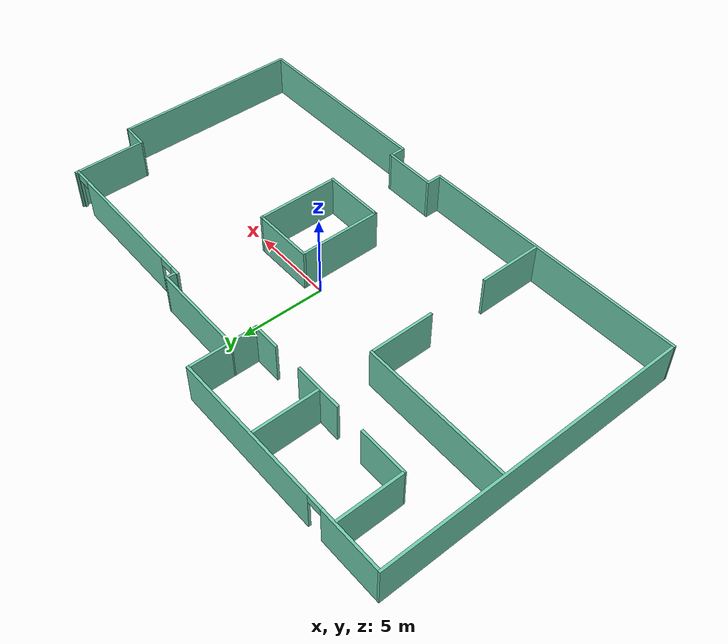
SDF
<?xml version='1.0'?>
<sdf version='1.7'>
  <model name='RAH-lab'>
    <link name='Wall_0'>
      <pose>-15.4096 -0.034118 0 0 0 -1.5708</pose>
      <self_collide>0</self_collide>
      <enable_wind>0</enable_wind>
      <kinematic>0</kinematic>
      <visual name='Wall_0_Visual'>
        <pose>0 0 1.25 0 -0 0</pose>
        <geometry>
          <box>
            <size>18.5837 0.15 2.5</size>
          </box>
        </geometry>
        <material>
          <diffuse>0.435294 0.796078 0.67451 1</diffuse>
          <specular>0.1 0.1 0.1 1</specular>
          <ambient>0.435294 0.796078 0.67451 1</ambient>
          <shader type='pixel'/>
        </material>
        <meta>
          <layer>0</layer>
        </meta>
        <transparency>0</transparency>
        <cast_shadows>1</cast_shadows>
      </visual>
      <collision name='Wall_0_Collision'>
        <laser_retro>0</laser_retro>
        <max_contacts>10</max_contacts>
        <pose>0 0 1.25 0 -0 0</pose>
        <geometry>
          <box>
            <size>18.5837 0.15 2.5</size>
          </box>
        </geometry>
        <surface>
          <friction>
            <ode>
              <mu>1</mu>
              <mu2>1</mu2>
              <fdir1>0 0 0</fdir1>
              <slip1>0</slip1>
              <slip2>0</slip2>
            </ode>
            <torsional>
              <coefficient>1</coefficient>
              <patch_radius>0</patch_radius>
              <surface_radius>0</surface_radius>
              <use_patch_radius>1</use_patch_radius>
              <ode>
                <slip>0</slip>
              </ode>
            </torsional>
          </friction>
          <bounce>
            <restitution_coefficient>0</restitution_coefficient>
            <threshold>1e+06</threshold>
          </bounce>
          <contact>
            <collide_without_contact>0</collide_without_contact>
            <collide_without_contact_bitmask>1</collide_without_contact_bitmask>
            <collide_bitmask>1</collide_bitmask>
            <ode>
              <soft_cfm>0</soft_cfm>
              <soft_erp>0.2</soft_erp>
              <kp>1e+13</kp>
              <kd>1</kd>
              <max_vel>0.01</max_vel>
              <min_depth>0</min_depth>
            </ode>
            <bullet>
              <split_impulse>1</split_impulse>
              <split_impulse_penetration_threshold>-0.01</split_impulse_penetration_threshold>
              <soft_cfm>0</soft_cfm>
              <soft_erp>0.2</soft_erp>
              <kp>1e+13</kp>
              <kd>1</kd>
            </bullet>
          </contact>
        </surface>
      </collision>
    </link>
    <link name='Wall_1'>
      <pose>-7.31852 -9.1806 0 0 -0 0.008695</pose>
      <self_collide>0</self_collide>
      <enable_wind>0</enable_wind>
      <kinematic>0</kinematic>
      <visual name='Wall_1_Visual'>
        <pose>0 0 1.25 0 -0 0</pose>
        <geometry>
          <box>
            <size>16.3328 0.15 2.5</size>
          </box>
        </geometry>
        <material>
          <diffuse>0.435294 0.796078 0.67451 1</diffuse>
          <specular>0.1 0.1 0.1 1</specular>
          <ambient>0.435294 0.796078 0.67451 1</ambient>
          <shader type='pixel'/>
        </material>
        <meta>
          <layer>0</layer>
        </meta>
        <transparency>0</transparency>
        <cast_shadows>1</cast_shadows>
      </visual>
      <collision name='Wall_1_Collision'>
        <laser_retro>0</laser_retro>
        <max_contacts>10</max_contacts>
        <pose>0 0 1.25 0 -0 0</pose>
        <geometry>
          <box>
            <size>16.3328 0.15 2.5</size>
          </box>
        </geometry>
        <surface>
          <friction>
            <ode>
              <mu>1</mu>
              <mu2>1</mu2>
              <fdir1>0 0 0</fdir1>
              <slip1>0</slip1>
              <slip2>0</slip2>
            </ode>
            <torsional>
              <coefficient>1</coefficient>
              <patch_radius>0</patch_radius>
              <surface_radius>0</surface_radius>
              <use_patch_radius>1</use_patch_radius>
              <ode>
                <slip>0</slip>
              </ode>
            </torsional>
          </friction>
          <bounce>
            <restitution_coefficient>0</restitution_coefficient>
            <threshold>1e+06</threshold>
          </bounce>
          <contact>
            <collide_without_contact>0</collide_without_contact>
            <collide_without_contact_bitmask>1</collide_without_contact_bitmask>
            <collide_bitmask>1</collide_bitmask>
            <ode>
              <soft_cfm>0</soft_cfm>
              <soft_erp>0.2</soft_erp>
              <kp>1e+13</kp>
              <kd>1</kd>
              <max_vel>0.01</max_vel>
              <min_depth>0</min_depth>
            </ode>
            <bullet>
              <split_impulse>1</split_impulse>
              <split_impulse_penetration_threshold>-0.01</split_impulse_penetration_threshold>
              <soft_cfm>0</soft_cfm>
              <soft_erp>0.2</soft_erp>
              <kp>1e+13</kp>
              <kd>1</kd>
            </bullet>
          </contact>
        </surface>
      </collision>
    </link>
    <link name='Wall_10'>
      <pose>3.82389 6.55251 0 0 -0 1.47981</pose>
      <self_collide>0</self_collide>
      <enable_wind>0</enable_wind>
      <kinematic>0</kinematic>
      <visual name='Wall_10_Visual'>
        <pose>0 0 1.25 0 -0 0</pose>
        <geometry>
          <box>
            <size>0.732199 0.15 2.5</size>
          </box>
        </geometry>
        <material>
          <diffuse>0.435294 0.796078 0.67451 1</diffuse>
          <specular>0.1 0.1 0.1 1</specular>
          <ambient>0.435294 0.796078 0.67451 1</ambient>
          <shader type='pixel'/>
        </material>
        <meta>
          <layer>0</layer>
        </meta>
        <transparency>0</transparency>
        <cast_shadows>1</cast_shadows>
      </visual>
      <collision name='Wall_10_Collision'>
        <laser_retro>0</laser_retro>
        <max_contacts>10</max_contacts>
        <pose>0 0 1.25 0 -0 0</pose>
        <geometry>
          <box>
            <size>0.732199 0.15 2.5</size>
          </box>
        </geometry>
        <surface>
          <friction>
            <ode>
              <mu>1</mu>
              <mu2>1</mu2>
              <fdir1>0 0 0</fdir1>
              <slip1>0</slip1>
              <slip2>0</slip2>
            </ode>
            <torsional>
              <coefficient>1</coefficient>
              <patch_radius>0</patch_radius>
              <surface_radius>0</surface_radius>
              <use_patch_radius>1</use_patch_radius>
              <ode>
                <slip>0</slip>
              </ode>
            </torsional>
          </friction>
          <bounce>
            <restitution_coefficient>0</restitution_coefficient>
            <threshold>1e+06</threshold>
          </bounce>
          <contact>
            <collide_without_contact>0</collide_without_contact>
            <collide_without_contact_bitmask>1</collide_without_contact_bitmask>
            <collide_bitmask>1</collide_bitmask>
            <ode>
              <soft_cfm>0</soft_cfm>
              <soft_erp>0.2</soft_erp>
              <kp>1e+13</kp>
              <kd>1</kd>
              <max_vel>0.01</max_vel>
              <min_depth>0</min_depth>
            </ode>
            <bullet>
              <split_impulse>1</split_impulse>
              <split_impulse_penetration_threshold>-0.01</split_impulse_penetration_threshold>
              <soft_cfm>0</soft_cfm>
              <soft_erp>0.2</soft_erp>
              <kp>1e+13</kp>
              <kd>1</kd>
            </bullet>
          </contact>
        </surface>
      </collision>
    </link>
    <link name='Wall_11'>
      <pose>1.02612 6.85661 0 0 -0 3.13647</pose>
      <self_collide>0</self_collide>
      <enable_wind>0</enable_wind>
      <kinematic>0</kinematic>
      <visual name='Wall_11_Visual'>
        <pose>0 0 1.25 0 -0 0</pose>
        <geometry>
          <box>
            <size>5.69272 0.15 2.5</size>
          </box>
        </geometry>
        <material>
          <diffuse>0.435294 0.796078 0.67451 1</diffuse>
          <specular>0.1 0.1 0.1 1</specular>
          <ambient>0.435294 0.796078 0.67451 1</ambient>
          <shader type='pixel'/>
        </material>
        <meta>
          <layer>0</layer>
        </meta>
        <transparency>0</transparency>
        <cast_shadows>1</cast_shadows>
      </visual>
      <collision name='Wall_11_Collision'>
        <laser_retro>0</laser_retro>
        <max_contacts>10</max_contacts>
        <pose>0 0 1.25 0 -0 0</pose>
        <geometry>
          <box>
            <size>5.69272 0.15 2.5</size>
          </box>
        </geometry>
        <surface>
          <friction>
            <ode>
              <mu>1</mu>
              <mu2>1</mu2>
              <fdir1>0 0 0</fdir1>
              <slip1>0</slip1>
              <slip2>0</slip2>
            </ode>
            <torsional>
              <coefficient>1</coefficient>
              <patch_radius>0</patch_radius>
              <surface_radius>0</surface_radius>
              <use_patch_radius>1</use_patch_radius>
              <ode>
                <slip>0</slip>
              </ode>
            </torsional>
          </friction>
          <bounce>
            <restitution_coefficient>0</restitution_coefficient>
            <threshold>1e+06</threshold>
          </bounce>
          <contact>
            <collide_without_contact>0</collide_without_contact>
            <collide_without_contact_bitmask>1</collide_without_contact_bitmask>
            <collide_bitmask>1</collide_bitmask>
            <ode>
              <soft_cfm>0</soft_cfm>
              <soft_erp>0.2</soft_erp>
              <kp>1e+13</kp>
              <kd>1</kd>
              <max_vel>0.01</max_vel>
              <min_depth>0</min_depth>
            </ode>
            <bullet>
              <split_impulse>1</split_impulse>
              <split_impulse_penetration_threshold>-0.01</split_impulse_penetration_threshold>
              <soft_cfm>0</soft_cfm>
              <soft_erp>0.2</soft_erp>
              <kp>1e+13</kp>
              <kd>1</kd>
            </bullet>
          </contact>
        </surface>
      </collision>
    </link>
    <link name='Wall_11_clone'>
      <pose>-10.8846 2.07703 0 0 -0 3.13647</pose>
      <self_collide>0</self_collide>
      <enable_wind>0</enable_wind>
      <kinematic>0</kinematic>
      <inertial>
        <inertia>
          <ixx>0</ixx>
          <ixy>0</ixy>
          <ixz>0</ixz>
          <iyy>0</iyy>
          <iyz>0</iyz>
          <izz>0</izz>
        </inertia>
        <mass>0</mass>
        <pose>0 0 0 0 -0 0</pose>
      </inertial>
      <visual name='Wall_11_Visual'>
        <pose>0 0 1.25 0 -0 0</pose>
        <geometry>
          <box>
            <size>8.90079 0.15 2.5</size>
          </box>
        </geometry>
        <material>
          <diffuse>0.435294 0.796078 0.67451 1</diffuse>
          <specular>0.1 0.1 0.1 1</specular>
          <ambient>0.435294 0.796078 0.67451 1</ambient>
          <shader type='pixel'/>
        </material>
        <meta>
          <layer>0</layer>
        </meta>
        <transparency>0</transparency>
        <cast_shadows>1</cast_shadows>
      </visual>
      <collision name='Wall_11_Collision'>
        <laser_retro>0</laser_retro>
        <max_contacts>10</max_contacts>
        <pose>0 0 1.25 0 -0 0</pose>
        <geometry>
          <box>
            <size>8.90079 0.15 2.5</size>
          </box>
        </geometry>
        <surface>
          <friction>
            <ode>
              <mu>1</mu>
              <mu2>1</mu2>
              <fdir1>0 0 0</fdir1>
              <slip1>0</slip1>
              <slip2>0</slip2>
            </ode>
            <torsional>
              <coefficient>1</coefficient>
              <patch_radius>0</patch_radius>
              <surface_radius>0</surface_radius>
              <use_patch_radius>1</use_patch_radius>
              <ode>
                <slip>0</slip>
              </ode>
            </torsional>
          </friction>
          <bounce>
            <restitution_coefficient>0</restitution_coefficient>
            <threshold>1e+06</threshold>
          </bounce>
          <contact>
            <collide_without_contact>0</collide_without_contact>
            <collide_without_contact_bitmask>1</collide_without_contact_bitmask>
            <collide_bitmask>1</collide_bitmask>
            <ode>
              <soft_cfm>0</soft_cfm>
              <soft_erp>0.2</soft_erp>
              <kp>1e+13</kp>
              <kd>1</kd>
              <max_vel>0.01</max_vel>
              <min_depth>0</min_depth>
            </ode>
            <bullet>
              <split_impulse>1</split_impulse>
              <split_impulse_penetration_threshold>-0.01</split_impulse_penetration_threshold>
              <soft_cfm>0</soft_cfm>
              <soft_erp>0.2</soft_erp>
              <kp>1e+13</kp>
              <kd>1</kd>
            </bullet>
          </contact>
        </surface>
      </collision>
    </link>
    <link name='Wall_11_clone_clone'>
      <pose>-6.52584 5.29616 0 0 -0 3.13647</pose>
      <self_collide>0</self_collide>
      <enable_wind>0</enable_wind>
      <kinematic>0</kinematic>
      <inertial>
        <inertia>
          <ixx>0</ixx>
          <ixy>0</ixy>
          <ixz>0</ixz>
          <iyy>0</iyy>
          <iyz>0</iyz>
          <izz>0</izz>
        </inertia>
        <mass>0</mass>
        <pose>0 0 0 0 -0 0</pose>
      </inertial>
      <visual name='Wall_11_Visual'>
        <pose>0 0 1.25 0 -0 0</pose>
        <geometry>
          <box>
            <size>2.93967 0.15 2.5</size>
          </box>
        </geometry>
        <material>
          <diffuse>0.435294 0.796078 0.67451 1</diffuse>
          <specular>0.1 0.1 0.1 1</specular>
          <ambient>0.435294 0.796078 0.67451 1</ambient>
          <shader type='pixel'/>
        </material>
        <meta>
          <layer>0</layer>
        </meta>
        <transparency>0</transparency>
        <cast_shadows>1</cast_shadows>
      </visual>
      <collision name='Wall_11_Collision'>
        <laser_retro>0</laser_retro>
        <max_contacts>10</max_contacts>
        <pose>0 0 1.25 0 -0 0</pose>
        <geometry>
          <box>
            <size>2.93967 0.15 2.5</size>
          </box>
        </geometry>
        <surface>
          <friction>
            <ode>
              <mu>1</mu>
              <mu2>1</mu2>
              <fdir1>0 0 0</fdir1>
              <slip1>0</slip1>
              <slip2>0</slip2>
            </ode>
            <torsional>
              <coefficient>1</coefficient>
              <patch_radius>0</patch_radius>
              <surface_radius>0</surface_radius>
              <use_patch_radius>1</use_patch_radius>
              <ode>
                <slip>0</slip>
              </ode>
            </torsional>
          </friction>
          <bounce>
            <restitution_coefficient>0</restitution_coefficient>
            <threshold>1e+06</threshold>
          </bounce>
          <contact>
            <collide_without_contact>0</collide_without_contact>
            <collide_without_contact_bitmask>1</collide_without_contact_bitmask>
            <collide_bitmask>1</collide_bitmask>
            <ode>
              <soft_cfm>0</soft_cfm>
              <soft_erp>0.2</soft_erp>
              <kp>1e+13</kp>
              <kd>1</kd>
              <max_vel>0.01</max_vel>
              <min_depth>0</min_depth>
            </ode>
            <bullet>
              <split_impulse>1</split_impulse>
              <split_impulse_penetration_threshold>-0.01</split_impulse_penetration_threshold>
              <soft_cfm>0</soft_cfm>
              <soft_erp>0.2</soft_erp>
              <kp>1e+13</kp>
              <kd>1</kd>
            </bullet>
          </contact>
        </surface>
      </collision>
    </link>
    <link name='Wall_11_clone_clone_0'>
      <pose>-11.1331 5.32306 0 0 -0 3.13647</pose>
      <self_collide>0</self_collide>
      <enable_wind>0</enable_wind>
      <kinematic>0</kinematic>
      <inertial>
        <inertia>
          <ixx>0</ixx>
          <ixy>0</ixy>
          <ixz>0</ixz>
          <iyy>0</iyy>
          <iyz>0</iyz>
          <izz>0</izz>
        </inertia>
        <mass>0</mass>
        <pose>0 0 0 0 -0 0</pose>
      </inertial>
      <visual name='Wall_11_Visual'>
        <pose>0 0 1.25 0 -0 0</pose>
        <geometry>
          <box>
            <size>2.92098 0.15 2.5</size>
          </box>
        </geometry>
        <material>
          <diffuse>0.435294 0.796078 0.67451 1</diffuse>
          <specular>0.1 0.1 0.1 1</specular>
          <ambient>0.435294 0.796078 0.67451 1</ambient>
          <shader type='pixel'/>
        </material>
        <meta>
          <layer>0</layer>
        </meta>
        <transparency>0</transparency>
        <cast_shadows>1</cast_shadows>
      </visual>
      <collision name='Wall_11_Collision'>
        <laser_retro>0</laser_retro>
        <max_contacts>10</max_contacts>
        <pose>0 0 1.25 0 -0 0</pose>
        <geometry>
          <box>
            <size>2.92098 0.15 2.5</size>
          </box>
        </geometry>
        <surface>
          <friction>
            <ode>
              <mu>1</mu>
              <mu2>1</mu2>
              <fdir1>0 0 0</fdir1>
              <slip1>0</slip1>
              <slip2>0</slip2>
            </ode>
            <torsional>
              <coefficient>1</coefficient>
              <patch_radius>0</patch_radius>
              <surface_radius>0</surface_radius>
              <use_patch_radius>1</use_patch_radius>
              <ode>
                <slip>0</slip>
              </ode>
            </torsional>
          </friction>
          <bounce>
            <restitution_coefficient>0</restitution_coefficient>
            <threshold>1e+06</threshold>
          </bounce>
          <contact>
            <collide_without_contact>0</collide_without_contact>
            <collide_without_contact_bitmask>1</collide_without_contact_bitmask>
            <collide_bitmask>1</collide_bitmask>
            <ode>
              <soft_cfm>0</soft_cfm>
              <soft_erp>0.2</soft_erp>
              <kp>1e+13</kp>
              <kd>1</kd>
              <max_vel>0.01</max_vel>
              <min_depth>0</min_depth>
            </ode>
            <bullet>
              <split_impulse>1</split_impulse>
              <split_impulse_penetration_threshold>-0.01</split_impulse_penetration_threshold>
              <soft_cfm>0</soft_cfm>
              <soft_erp>0.2</soft_erp>
              <kp>1e+13</kp>
              <kd>1</kd>
            </bullet>
          </contact>
        </surface>
      </collision>
    </link>
    <link name='Wall_11_clone_clone_0_clone'>
      <pose>-2.51918 5.31988 0 0 -0 3.13647</pose>
      <self_collide>0</self_collide>
      <enable_wind>0</enable_wind>
      <kinematic>0</kinematic>
      <inertial>
        <inertia>
          <ixx>0</ixx>
          <ixy>0</ixy>
          <ixz>0</ixz>
          <iyy>0</iyy>
          <iyz>0</iyz>
          <izz>0</izz>
        </inertia>
        <mass>0</mass>
        <pose>0 0 0 0 -0 0</pose>
      </inertial>
      <visual name='Wall_11_Visual'>
        <pose>0 0 1.25 0 -0 0</pose>
        <geometry>
          <box>
            <size>1.71262 0.15 2.5</size>
          </box>
        </geometry>
        <material>
          <diffuse>0.435294 0.796078 0.67451 1</diffuse>
          <specular>0.1 0.1 0.1 1</specular>
          <ambient>0.435294 0.796078 0.67451 1</ambient>
          <shader type='pixel'/>
        </material>
        <meta>
          <layer>0</layer>
        </meta>
        <transparency>0</transparency>
        <cast_shadows>1</cast_shadows>
      </visual>
      <collision name='Wall_11_Collision'>
        <laser_retro>0</laser_retro>
        <max_contacts>10</max_contacts>
        <pose>0 0 1.25 0 -0 0</pose>
        <geometry>
          <box>
            <size>1.71262 0.15 2.5</size>
          </box>
        </geometry>
        <surface>
          <friction>
            <ode>
              <mu>1</mu>
              <mu2>1</mu2>
              <fdir1>0 0 0</fdir1>
              <slip1>0</slip1>
              <slip2>0</slip2>
            </ode>
            <torsional>
              <coefficient>1</coefficient>
              <patch_radius>0</patch_radius>
              <surface_radius>0</surface_radius>
              <use_patch_radius>1</use_patch_radius>
              <ode>
                <slip>0</slip>
              </ode>
            </torsional>
          </friction>
          <bounce>
            <restitution_coefficient>0</restitution_coefficient>
            <threshold>1e+06</threshold>
          </bounce>
          <contact>
            <collide_without_contact>0</collide_without_contact>
            <collide_without_contact_bitmask>1</collide_without_contact_bitmask>
            <collide_bitmask>1</collide_bitmask>
            <ode>
              <soft_cfm>0</soft_cfm>
              <soft_erp>0.2</soft_erp>
              <kp>1e+13</kp>
              <kd>1</kd>
              <max_vel>0.01</max_vel>
              <min_depth>0</min_depth>
            </ode>
            <bullet>
              <split_impulse>1</split_impulse>
              <split_impulse_penetration_threshold>-0.01</split_impulse_penetration_threshold>
              <soft_cfm>0</soft_cfm>
              <soft_erp>0.2</soft_erp>
              <kp>1e+13</kp>
              <kd>1</kd>
            </bullet>
          </contact>
        </surface>
      </collision>
    </link>
    <link name='Wall_12'>
      <pose>-1.7452 7.26941 0 0 -0 1.5708</pose>
      <self_collide>0</self_collide>
      <enable_wind>0</enable_wind>
      <kinematic>0</kinematic>
      <inertial>
        <inertia>
          <ixx>0</ixx>
          <ixy>0</ixy>
          <ixz>0</ixz>
          <iyy>0</iyy>
          <iyz>0</iyz>
          <izz>0</izz>
        </inertia>
        <mass>0</mass>
        <pose>0 0 0 0 -0 0</pose>
      </inertial>
      <visual name='Wall_12_Visual'>
        <pose>0 0 1.25 0 -0 0</pose>
        <geometry>
          <box>
            <size>3.84217 0.15 2.5</size>
          </box>
        </geometry>
        <material>
          <diffuse>0.435294 0.796078 0.67451 1</diffuse>
          <specular>0.1 0.1 0.1 1</specular>
          <ambient>0.435294 0.796078 0.67451 1</ambient>
          <shader type='pixel'/>
        </material>
        <meta>
          <layer>0</layer>
        </meta>
        <transparency>0</transparency>
        <cast_shadows>1</cast_shadows>
      </visual>
      <collision name='Wall_12_Collision'>
        <laser_retro>0</laser_retro>
        <max_contacts>10</max_contacts>
        <pose>0 0 1.25 0 -0 0</pose>
        <geometry>
          <box>
            <size>3.84217 0.15 2.5</size>
          </box>
        </geometry>
        <surface>
          <friction>
            <ode>
              <mu>1</mu>
              <mu2>1</mu2>
              <fdir1>0 0 0</fdir1>
              <slip1>0</slip1>
              <slip2>0</slip2>
            </ode>
            <torsional>
              <coefficient>1</coefficient>
              <patch_radius>0</patch_radius>
              <surface_radius>0</surface_radius>
              <use_patch_radius>1</use_patch_radius>
              <ode>
                <slip>0</slip>
              </ode>
            </torsional>
          </friction>
          <bounce>
            <restitution_coefficient>0</restitution_coefficient>
            <threshold>1e+06</threshold>
          </bounce>
          <contact>
            <collide_without_contact>0</collide_without_contact>
            <collide_without_contact_bitmask>1</collide_without_contact_bitmask>
            <collide_bitmask>1</collide_bitmask>
            <ode>
              <soft_cfm>0</soft_cfm>
              <soft_erp>0.2</soft_erp>
              <kp>1e+13</kp>
              <kd>1</kd>
              <max_vel>0.01</max_vel>
              <min_depth>0</min_depth>
            </ode>
            <bullet>
              <split_impulse>1</split_impulse>
              <split_impulse_penetration_threshold>-0.01</split_impulse_penetration_threshold>
              <soft_cfm>0</soft_cfm>
              <soft_erp>0.2</soft_erp>
              <kp>1e+13</kp>
              <kd>1</kd>
            </bullet>
          </contact>
        </surface>
      </collision>
    </link>
    <link name='Wall_12_clone'>
      <pose>-12.5281 7.24833 0 0 -0 1.5708</pose>
      <self_collide>0</self_collide>
      <enable_wind>0</enable_wind>
      <kinematic>0</kinematic>
      <inertial>
        <inertia>
          <ixx>0</ixx>
          <ixy>0</ixy>
          <ixz>0</ixz>
          <iyy>0</iyy>
          <iyz>0</iyz>
          <izz>0</izz>
        </inertia>
        <mass>0</mass>
        <pose>0 0 0 0 -0 0</pose>
      </inertial>
      <visual name='Wall_12_Visual'>
        <pose>0 0 1.25 0 -0 0</pose>
        <geometry>
          <box>
            <size>3.7853 0.15 2.5</size>
          </box>
        </geometry>
        <material>
          <diffuse>0.435294 0.796078 0.67451 1</diffuse>
          <specular>0.1 0.1 0.1 1</specular>
          <ambient>0.435294 0.796078 0.67451 1</ambient>
          <shader type='pixel'/>
        </material>
        <meta>
          <layer>0</layer>
        </meta>
        <transparency>0</transparency>
        <cast_shadows>1</cast_shadows>
      </visual>
      <collision name='Wall_12_Collision'>
        <laser_retro>0</laser_retro>
        <max_contacts>10</max_contacts>
        <pose>0 0 1.25 0 -0 0</pose>
        <geometry>
          <box>
            <size>3.7853 0.15 2.5</size>
          </box>
        </geometry>
        <surface>
          <friction>
            <ode>
              <mu>1</mu>
              <mu2>1</mu2>
              <fdir1>0 0 0</fdir1>
              <slip1>0</slip1>
              <slip2>0</slip2>
            </ode>
            <torsional>
              <coefficient>1</coefficient>
              <patch_radius>0</patch_radius>
              <surface_radius>0</surface_radius>
              <use_patch_radius>1</use_patch_radius>
              <ode>
                <slip>0</slip>
              </ode>
            </torsional>
          </friction>
          <bounce>
            <restitution_coefficient>0</restitution_coefficient>
            <threshold>1e+06</threshold>
          </bounce>
          <contact>
            <collide_without_contact>0</collide_without_contact>
            <collide_without_contact_bitmask>1</collide_without_contact_bitmask>
            <collide_bitmask>1</collide_bitmask>
            <ode>
              <soft_cfm>0</soft_cfm>
              <soft_erp>0.2</soft_erp>
              <kp>1e+13</kp>
              <kd>1</kd>
              <max_vel>0.01</max_vel>
              <min_depth>0</min_depth>
            </ode>
            <bullet>
              <split_impulse>1</split_impulse>
              <split_impulse_penetration_threshold>-0.01</split_impulse_penetration_threshold>
              <soft_cfm>0</soft_cfm>
              <soft_erp>0.2</soft_erp>
              <kp>1e+13</kp>
              <kd>1</kd>
            </bullet>
          </contact>
        </surface>
      </collision>
    </link>
    <link name='Wall_12_clone_clone'>
      <pose>-6.66495 7.25378 0 0 -0 1.5708</pose>
      <self_collide>0</self_collide>
      <enable_wind>0</enable_wind>
      <kinematic>0</kinematic>
      <inertial>
        <inertia>
          <ixx>0</ixx>
          <ixy>0</ixy>
          <ixz>0</ixz>
          <iyy>0</iyy>
          <iyz>0</iyz>
          <izz>0</izz>
        </inertia>
        <mass>0</mass>
        <pose>0 0 0 0 -0 0</pose>
      </inertial>
      <visual name='Wall_12_Visual'>
        <pose>0 0 1.25 0 -0 0</pose>
        <geometry>
          <box>
            <size>3.7853 0.15 2.5</size>
          </box>
        </geometry>
        <material>
          <diffuse>0.435294 0.796078 0.67451 1</diffuse>
          <specular>0.1 0.1 0.1 1</specular>
          <ambient>0.435294 0.796078 0.67451 1</ambient>
          <shader type='pixel'/>
        </material>
        <meta>
          <layer>0</layer>
        </meta>
        <transparency>0</transparency>
        <cast_shadows>1</cast_shadows>
      </visual>
      <collision name='Wall_12_Collision'>
        <laser_retro>0</laser_retro>
        <max_contacts>10</max_contacts>
        <pose>0 0 1.25 0 -0 0</pose>
        <geometry>
          <box>
            <size>3.7853 0.15 2.5</size>
          </box>
        </geometry>
        <surface>
          <friction>
            <ode>
              <mu>1</mu>
              <mu2>1</mu2>
              <fdir1>0 0 0</fdir1>
              <slip1>0</slip1>
              <slip2>0</slip2>
            </ode>
            <torsional>
              <coefficient>1</coefficient>
              <patch_radius>0</patch_radius>
              <surface_radius>0</surface_radius>
              <use_patch_radius>1</use_patch_radius>
              <ode>
                <slip>0</slip>
              </ode>
            </torsional>
          </friction>
          <bounce>
            <restitution_coefficient>0</restitution_coefficient>
            <threshold>1e+06</threshold>
          </bounce>
          <contact>
            <collide_without_contact>0</collide_without_contact>
            <collide_without_contact_bitmask>1</collide_without_contact_bitmask>
            <collide_bitmask>1</collide_bitmask>
            <ode>
              <soft_cfm>0</soft_cfm>
              <soft_erp>0.2</soft_erp>
              <kp>1e+13</kp>
              <kd>1</kd>
              <max_vel>0.01</max_vel>
              <min_depth>0</min_depth>
            </ode>
            <bullet>
              <split_impulse>1</split_impulse>
              <split_impulse_penetration_threshold>-0.01</split_impulse_penetration_threshold>
              <soft_cfm>0</soft_cfm>
              <soft_erp>0.2</soft_erp>
              <kp>1e+13</kp>
              <kd>1</kd>
            </bullet>
          </contact>
        </surface>
      </collision>
    </link>
    <link name='Wall_12_clone_clone_clone'>
      <pose>-6.50385 0.079986 0 0 -0 1.5708</pose>
      <self_collide>0</self_collide>
      <enable_wind>0</enable_wind>
      <kinematic>0</kinematic>
      <inertial>
        <inertia>
          <ixx>0</ixx>
          <ixy>0</ixy>
          <ixz>0</ixz>
          <iyy>0</iyy>
          <iyz>0</iyz>
          <izz>0</izz>
        </inertia>
        <mass>0</mass>
        <pose>0 0 0 0 -0 0</pose>
      </inertial>
      <visual name='Wall_12_Visual'>
        <pose>0 0 1.25 0 -0 0</pose>
        <geometry>
          <box>
            <size>3.7853 0.15 2.5</size>
          </box>
        </geometry>
        <material>
          <diffuse>0.435294 0.796078 0.67451 1</diffuse>
          <specular>0.1 0.1 0.1 1</specular>
          <ambient>0.435294 0.796078 0.67451 1</ambient>
          <shader type='pixel'/>
        </material>
        <meta>
          <layer>0</layer>
        </meta>
        <transparency>0</transparency>
        <cast_shadows>1</cast_shadows>
      </visual>
      <collision name='Wall_12_Collision'>
        <laser_retro>0</laser_retro>
        <max_contacts>10</max_contacts>
        <pose>0 0 1.25 0 -0 0</pose>
        <geometry>
          <box>
            <size>3.7853 0.15 2.5</size>
          </box>
        </geometry>
        <surface>
          <friction>
            <ode>
              <mu>1</mu>
              <mu2>1</mu2>
              <fdir1>0 0 0</fdir1>
              <slip1>0</slip1>
              <slip2>0</slip2>
            </ode>
            <torsional>
              <coefficient>1</coefficient>
              <patch_radius>0</patch_radius>
              <surface_radius>0</surface_radius>
              <use_patch_radius>1</use_patch_radius>
              <ode>
                <slip>0</slip>
              </ode>
            </torsional>
          </friction>
          <bounce>
            <restitution_coefficient>0</restitution_coefficient>
            <threshold>1e+06</threshold>
          </bounce>
          <contact>
            <collide_without_contact>0</collide_without_contact>
            <collide_without_contact_bitmask>1</collide_without_contact_bitmask>
            <collide_bitmask>1</collide_bitmask>
            <ode>
              <soft_cfm>0</soft_cfm>
              <soft_erp>0.2</soft_erp>
              <kp>1e+13</kp>
              <kd>1</kd>
              <max_vel>0.01</max_vel>
              <min_depth>0</min_depth>
            </ode>
            <bullet>
              <split_impulse>1</split_impulse>
              <split_impulse_penetration_threshold>-0.01</split_impulse_penetration_threshold>
              <soft_cfm>0</soft_cfm>
              <soft_erp>0.2</soft_erp>
              <kp>1e+13</kp>
              <kd>1</kd>
            </bullet>
          </contact>
        </surface>
      </collision>
    </link>
    <link name='Wall_12_clone_clone_clone_0'>
      <pose>-6.53494 -7.24529 0 0 -0 1.5708</pose>
      <self_collide>0</self_collide>
      <enable_wind>0</enable_wind>
      <kinematic>0</kinematic>
      <inertial>
        <inertia>
          <ixx>0</ixx>
          <ixy>0</ixy>
          <ixz>0</ixz>
          <iyy>0</iyy>
          <iyz>0</iyz>
          <izz>0</izz>
        </inertia>
        <mass>0</mass>
        <pose>0 0 0 0 -0 0</pose>
      </inertial>
      <visual name='Wall_12_Visual'>
        <pose>0 0 1.25 0 -0 0</pose>
        <geometry>
          <box>
            <size>3.7853 0.15 2.5</size>
          </box>
        </geometry>
        <material>
          <diffuse>0.435294 0.796078 0.67451 1</diffuse>
          <specular>0.1 0.1 0.1 1</specular>
          <ambient>0.435294 0.796078 0.67451 1</ambient>
          <shader type='pixel'/>
        </material>
        <meta>
          <layer>0</layer>
        </meta>
        <transparency>0</transparency>
        <cast_shadows>1</cast_shadows>
      </visual>
      <collision name='Wall_12_Collision'>
        <laser_retro>0</laser_retro>
        <max_contacts>10</max_contacts>
        <pose>0 0 1.25 0 -0 0</pose>
        <geometry>
          <box>
            <size>3.7853 0.15 2.5</size>
          </box>
        </geometry>
        <surface>
          <friction>
            <ode>
              <mu>1</mu>
              <mu2>1</mu2>
              <fdir1>0 0 0</fdir1>
              <slip1>0</slip1>
              <slip2>0</slip2>
            </ode>
            <torsional>
              <coefficient>1</coefficient>
              <patch_radius>0</patch_radius>
              <surface_radius>0</surface_radius>
              <use_patch_radius>1</use_patch_radius>
              <ode>
                <slip>0</slip>
              </ode>
            </torsional>
          </friction>
          <bounce>
            <restitution_coefficient>0</restitution_coefficient>
            <threshold>1e+06</threshold>
          </bounce>
          <contact>
            <collide_without_contact>0</collide_without_contact>
            <collide_without_contact_bitmask>1</collide_without_contact_bitmask>
            <collide_bitmask>1</collide_bitmask>
            <ode>
              <soft_cfm>0</soft_cfm>
              <soft_erp>0.2</soft_erp>
              <kp>1e+13</kp>
              <kd>1</kd>
              <max_vel>0.01</max_vel>
              <min_depth>0</min_depth>
            </ode>
            <bullet>
              <split_impulse>1</split_impulse>
              <split_impulse_penetration_threshold>-0.01</split_impulse_penetration_threshold>
              <soft_cfm>0</soft_cfm>
              <soft_erp>0.2</soft_erp>
              <kp>1e+13</kp>
              <kd>1</kd>
            </bullet>
          </contact>
        </surface>
      </collision>
    </link>
    <link name='Wall_13'>
      <pose>-8.547 9.21697 0 0 0 -3.13656</pose>
      <self_collide>0</self_collide>
      <enable_wind>0</enable_wind>
      <kinematic>0</kinematic>
      <inertial>
        <inertia>
          <ixx>0</ixx>
          <ixy>0</ixy>
          <ixz>0</ixz>
          <iyy>0</iyy>
          <iyz>0</iyz>
          <izz>0</izz>
        </inertia>
        <mass>0</mass>
        <pose>0 0 0 0 -0 0</pose>
      </inertial>
      <visual name='Wall_13_Visual_0'>
        <pose>-2.32309 0 1.25 0 -0 0</pose>
        <geometry>
          <box>
            <size>9.12865 0.15 2.5</size>
          </box>
        </geometry>
        <material>
          <diffuse>0.435294 0.796078 0.67451 1</diffuse>
          <specular>0.1 0.1 0.1 1</specular>
          <ambient>0.435294 0.796078 0.67451 1</ambient>
          <shader type='pixel'/>
        </material>
        <meta>
          <layer>0</layer>
        </meta>
        <transparency>0</transparency>
        <cast_shadows>1</cast_shadows>
      </visual>
      <visual name='Wall_13_Visual_1'>
        <pose>5.00383 0 1.25 0 -0 0</pose>
        <geometry>
          <box>
            <size>3.75481 0.15 2.5</size>
          </box>
        </geometry>
        <material>
          <diffuse>0.435294 0.796078 0.67451 1</diffuse>
          <specular>0.1 0.1 0.1 1</specular>
          <ambient>0.435294 0.796078 0.67451 1</ambient>
          <shader type='pixel'/>
        </material>
        <meta>
          <layer>0</layer>
        </meta>
        <transparency>0</transparency>
        <cast_shadows>1</cast_shadows>
      </visual>
      <visual name='Wall_13_Visual_2'>
        <pose>2.68074 0 2.25 0 -0 0</pose>
        <geometry>
          <box>
            <size>0.902032 0.15 0.5</size>
          </box>
        </geometry>
        <material>
          <diffuse>0.435294 0.796078 0.67451 1</diffuse>
          <specular>0.1 0.1 0.1 1</specular>
          <ambient>0.435294 0.796078 0.67451 1</ambient>
          <shader type='pixel'/>
        </material>
        <meta>
          <layer>0</layer>
        </meta>
        <transparency>0</transparency>
        <cast_shadows>1</cast_shadows>
      </visual>
      <collision name='Wall_13_Collision_0'>
        <laser_retro>0</laser_retro>
        <max_contacts>10</max_contacts>
        <pose>-2.32309 0 1.25 0 -0 0</pose>
        <geometry>
          <box>
            <size>9.12865 0.15 2.5</size>
          </box>
        </geometry>
        <surface>
          <friction>
            <ode>
              <mu>1</mu>
              <mu2>1</mu2>
              <fdir1>0 0 0</fdir1>
              <slip1>0</slip1>
              <slip2>0</slip2>
            </ode>
            <torsional>
              <coefficient>1</coefficient>
              <patch_radius>0</patch_radius>
              <surface_radius>0</surface_radius>
              <use_patch_radius>1</use_patch_radius>
              <ode>
                <slip>0</slip>
              </ode>
            </torsional>
          </friction>
          <bounce>
            <restitution_coefficient>0</restitution_coefficient>
            <threshold>1e+06</threshold>
          </bounce>
          <contact>
            <collide_without_contact>0</collide_without_contact>
            <collide_without_contact_bitmask>1</collide_without_contact_bitmask>
            <collide_bitmask>1</collide_bitmask>
            <ode>
              <soft_cfm>0</soft_cfm>
              <soft_erp>0.2</soft_erp>
              <kp>1e+13</kp>
              <kd>1</kd>
              <max_vel>0.01</max_vel>
              <min_depth>0</min_depth>
            </ode>
            <bullet>
              <split_impulse>1</split_impulse>
              <split_impulse_penetration_threshold>-0.01</split_impulse_penetration_threshold>
              <soft_cfm>0</soft_cfm>
              <soft_erp>0.2</soft_erp>
              <kp>1e+13</kp>
              <kd>1</kd>
            </bullet>
          </contact>
        </surface>
      </collision>
      <collision name='Wall_13_Collision_2'>
        <laser_retro>0</laser_retro>
        <max_contacts>10</max_contacts>
        <pose>2.68074 0 2.25 0 -0 0</pose>
        <geometry>
          <box>
            <size>0.902032 0.15 0.5</size>
          </box>
        </geometry>
        <surface>
          <friction>
            <ode>
              <mu>1</mu>
              <mu2>1</mu2>
              <fdir1>0 0 0</fdir1>
              <slip1>0</slip1>
              <slip2>0</slip2>
            </ode>
            <torsional>
              <coefficient>1</coefficient>
              <patch_radius>0</patch_radius>
              <surface_radius>0</surface_radius>
              <use_patch_radius>1</use_patch_radius>
              <ode>
                <slip>0</slip>
              </ode>
            </torsional>
          </friction>
          <bounce>
            <restitution_coefficient>0</restitution_coefficient>
            <threshold>1e+06</threshold>
          </bounce>
          <contact>
            <collide_without_contact>0</collide_without_contact>
            <collide_without_contact_bitmask>1</collide_without_contact_bitmask>
            <collide_bitmask>1</collide_bitmask>
            <ode>
              <soft_cfm>0</soft_cfm>
              <soft_erp>0.2</soft_erp>
              <kp>1e+13</kp>
              <kd>1</kd>
              <max_vel>0.01</max_vel>
              <min_depth>0</min_depth>
            </ode>
            <bullet>
              <split_impulse>1</split_impulse>
              <split_impulse_penetration_threshold>-0.01</split_impulse_penetration_threshold>
              <soft_cfm>0</soft_cfm>
              <soft_erp>0.2</soft_erp>
              <kp>1e+13</kp>
              <kd>1</kd>
            </bullet>
          </contact>
        </surface>
      </collision>
      <collision name='Wall_13_Collision_1'>
        <laser_retro>0</laser_retro>
        <max_contacts>10</max_contacts>
        <pose>5.00383 0 1.25 0 -0 0</pose>
        <geometry>
          <box>
            <size>3.75481 0.15 2.5</size>
          </box>
        </geometry>
        <surface>
          <friction>
            <ode>
              <mu>1</mu>
              <mu2>1</mu2>
              <fdir1>0 0 0</fdir1>
              <slip1>0</slip1>
              <slip2>0</slip2>
            </ode>
            <torsional>
              <coefficient>1</coefficient>
              <patch_radius>0</patch_radius>
              <surface_radius>0</surface_radius>
              <use_patch_radius>1</use_patch_radius>
              <ode>
                <slip>0</slip>
              </ode>
            </torsional>
          </friction>
          <bounce>
            <restitution_coefficient>0</restitution_coefficient>
            <threshold>1e+06</threshold>
          </bounce>
          <contact>
            <collide_without_contact>0</collide_without_contact>
            <collide_without_contact_bitmask>1</collide_without_contact_bitmask>
            <collide_bitmask>1</collide_bitmask>
            <ode>
              <soft_cfm>0</soft_cfm>
              <soft_erp>0.2</soft_erp>
              <kp>1e+13</kp>
              <kd>1</kd>
              <max_vel>0.01</max_vel>
              <min_depth>0</min_depth>
            </ode>
            <bullet>
              <split_impulse>1</split_impulse>
              <split_impulse_penetration_threshold>-0.01</split_impulse_penetration_threshold>
              <soft_cfm>0</soft_cfm>
              <soft_erp>0.2</soft_erp>
              <kp>1e+13</kp>
              <kd>1</kd>
            </bullet>
          </contact>
        </surface>
      </collision>
    </link>
    <link name='Wall_15'>
      <pose>0.761931 -1.9537 0 0 0 -1.5708</pose>
      <self_collide>0</self_collide>
      <enable_wind>0</enable_wind>
      <kinematic>0</kinematic>
      <visual name='Wall_15_Visual'>
        <pose>0 0 1.25 0 -0 0</pose>
        <geometry>
          <box>
            <size>5 0.15 2.5</size>
          </box>
        </geometry>
        <material>
          <diffuse>0.435294 0.796078 0.67451 1</diffuse>
          <specular>0.1 0.1 0.1 1</specular>
          <ambient>0.435294 0.796078 0.67451 1</ambient>
          <shader type='pixel'/>
        </material>
        <meta>
          <layer>0</layer>
        </meta>
        <transparency>0</transparency>
        <cast_shadows>1</cast_shadows>
      </visual>
      <collision name='Wall_15_Collision'>
        <laser_retro>0</laser_retro>
        <max_contacts>10</max_contacts>
        <pose>0 0 1.25 0 -0 0</pose>
        <geometry>
          <box>
            <size>5 0.15 2.5</size>
          </box>
        </geometry>
        <surface>
          <friction>
            <ode>
              <mu>1</mu>
              <mu2>1</mu2>
              <fdir1>0 0 0</fdir1>
              <slip1>0</slip1>
              <slip2>0</slip2>
            </ode>
            <torsional>
              <coefficient>1</coefficient>
              <patch_radius>0</patch_radius>
              <surface_radius>0</surface_radius>
              <use_patch_radius>1</use_patch_radius>
              <ode>
                <slip>0</slip>
              </ode>
            </torsional>
          </friction>
          <bounce>
            <restitution_coefficient>0</restitution_coefficient>
            <threshold>1e+06</threshold>
          </bounce>
          <contact>
            <collide_without_contact>0</collide_without_contact>
            <collide_without_contact_bitmask>1</collide_without_contact_bitmask>
            <collide_bitmask>1</collide_bitmask>
            <ode>
              <soft_cfm>0</soft_cfm>
              <soft_erp>0.2</soft_erp>
              <kp>1e+13</kp>
              <kd>1</kd>
              <max_vel>0.01</max_vel>
              <min_depth>0</min_depth>
            </ode>
            <bullet>
              <split_impulse>1</split_impulse>
              <split_impulse_penetration_threshold>-0.01</split_impulse_penetration_threshold>
              <soft_cfm>0</soft_cfm>
              <soft_erp>0.2</soft_erp>
              <kp>1e+13</kp>
              <kd>1</kd>
            </bullet>
          </contact>
        </surface>
      </collision>
    </link>
    <link name='Wall_16'>
      <pose>2.56193 -4.3787 0 0 -0 0</pose>
      <self_collide>0</self_collide>
      <enable_wind>0</enable_wind>
      <kinematic>0</kinematic>
      <visual name='Wall_16_Visual'>
        <pose>0 0 1.25 0 -0 0</pose>
        <geometry>
          <box>
            <size>3.75 0.15 2.5</size>
          </box>
        </geometry>
        <material>
          <diffuse>0.435294 0.796078 0.67451 1</diffuse>
          <specular>0.1 0.1 0.1 1</specular>
          <ambient>0.435294 0.796078 0.67451 1</ambient>
          <shader type='pixel'/>
        </material>
        <meta>
          <layer>0</layer>
        </meta>
        <transparency>0</transparency>
        <cast_shadows>1</cast_shadows>
      </visual>
      <collision name='Wall_16_Collision'>
        <laser_retro>0</laser_retro>
        <max_contacts>10</max_contacts>
        <pose>0 0 1.25 0 -0 0</pose>
        <geometry>
          <box>
            <size>3.75 0.15 2.5</size>
          </box>
        </geometry>
        <surface>
          <friction>
            <ode>
              <mu>1</mu>
              <mu2>1</mu2>
              <fdir1>0 0 0</fdir1>
              <slip1>0</slip1>
              <slip2>0</slip2>
            </ode>
            <torsional>
              <coefficient>1</coefficient>
              <patch_radius>0</patch_radius>
              <surface_radius>0</surface_radius>
              <use_patch_radius>1</use_patch_radius>
              <ode>
                <slip>0</slip>
              </ode>
            </torsional>
          </friction>
          <bounce>
            <restitution_coefficient>0</restitution_coefficient>
            <threshold>1e+06</threshold>
          </bounce>
          <contact>
            <collide_without_contact>0</collide_without_contact>
            <collide_without_contact_bitmask>1</collide_without_contact_bitmask>
            <collide_bitmask>1</collide_bitmask>
            <ode>
              <soft_cfm>0</soft_cfm>
              <soft_erp>0.2</soft_erp>
              <kp>1e+13</kp>
              <kd>1</kd>
              <max_vel>0.01</max_vel>
              <min_depth>0</min_depth>
            </ode>
            <bullet>
              <split_impulse>1</split_impulse>
              <split_impulse_penetration_threshold>-0.01</split_impulse_penetration_threshold>
              <soft_cfm>0</soft_cfm>
              <soft_erp>0.2</soft_erp>
              <kp>1e+13</kp>
              <kd>1</kd>
            </bullet>
          </contact>
        </surface>
      </collision>
    </link>
    <link name='Wall_17'>
      <pose>4.36193 -1.9537 0 0 -0 1.5708</pose>
      <self_collide>0</self_collide>
      <enable_wind>0</enable_wind>
      <kinematic>0</kinematic>
      <visual name='Wall_17_Visual'>
        <pose>0 0 1.25 0 -0 0</pose>
        <geometry>
          <box>
            <size>5 0.15 2.5</size>
          </box>
        </geometry>
        <material>
          <diffuse>0.435294 0.796078 0.67451 1</diffuse>
          <specular>0.1 0.1 0.1 1</specular>
          <ambient>0.435294 0.796078 0.67451 1</ambient>
          <shader type='pixel'/>
        </material>
        <meta>
          <layer>0</layer>
        </meta>
        <transparency>0</transparency>
        <cast_shadows>1</cast_shadows>
      </visual>
      <collision name='Wall_17_Collision'>
        <laser_retro>0</laser_retro>
        <max_contacts>10</max_contacts>
        <pose>0 0 1.25 0 -0 0</pose>
        <geometry>
          <box>
            <size>5 0.15 2.5</size>
          </box>
        </geometry>
        <surface>
          <friction>
            <ode>
              <mu>1</mu>
              <mu2>1</mu2>
              <fdir1>0 0 0</fdir1>
              <slip1>0</slip1>
              <slip2>0</slip2>
            </ode>
            <torsional>
              <coefficient>1</coefficient>
              <patch_radius>0</patch_radius>
              <surface_radius>0</surface_radius>
              <use_patch_radius>1</use_patch_radius>
              <ode>
                <slip>0</slip>
              </ode>
            </torsional>
          </friction>
          <bounce>
            <restitution_coefficient>0</restitution_coefficient>
            <threshold>1e+06</threshold>
          </bounce>
          <contact>
            <collide_without_contact>0</collide_without_contact>
            <collide_without_contact_bitmask>1</collide_without_contact_bitmask>
            <collide_bitmask>1</collide_bitmask>
            <ode>
              <soft_cfm>0</soft_cfm>
              <soft_erp>0.2</soft_erp>
              <kp>1e+13</kp>
              <kd>1</kd>
              <max_vel>0.01</max_vel>
              <min_depth>0</min_depth>
            </ode>
            <bullet>
              <split_impulse>1</split_impulse>
              <split_impulse_penetration_threshold>-0.01</split_impulse_penetration_threshold>
              <soft_cfm>0</soft_cfm>
              <soft_erp>0.2</soft_erp>
              <kp>1e+13</kp>
              <kd>1</kd>
            </bullet>
          </contact>
        </surface>
      </collision>
    </link>
    <link name='Wall_18'>
      <pose>2.56193 0.471296 0 0 -0 3.14159</pose>
      <self_collide>0</self_collide>
      <enable_wind>0</enable_wind>
      <kinematic>0</kinematic>
      <visual name='Wall_18_Visual'>
        <pose>0 0 1.25 0 -0 0</pose>
        <geometry>
          <box>
            <size>3.75 0.15 2.5</size>
          </box>
        </geometry>
        <material>
          <diffuse>0.435294 0.796078 0.67451 1</diffuse>
          <specular>0.1 0.1 0.1 1</specular>
          <ambient>0.435294 0.796078 0.67451 1</ambient>
          <shader type='pixel'/>
        </material>
        <meta>
          <layer>0</layer>
        </meta>
        <transparency>0</transparency>
        <cast_shadows>1</cast_shadows>
      </visual>
      <collision name='Wall_18_Collision'>
        <laser_retro>0</laser_retro>
        <max_contacts>10</max_contacts>
        <pose>0 0 1.25 0 -0 0</pose>
        <geometry>
          <box>
            <size>3.75 0.15 2.5</size>
          </box>
        </geometry>
        <surface>
          <friction>
            <ode>
              <mu>1</mu>
              <mu2>1</mu2>
              <fdir1>0 0 0</fdir1>
              <slip1>0</slip1>
              <slip2>0</slip2>
            </ode>
            <torsional>
              <coefficient>1</coefficient>
              <patch_radius>0</patch_radius>
              <surface_radius>0</surface_radius>
              <use_patch_radius>1</use_patch_radius>
              <ode>
                <slip>0</slip>
              </ode>
            </torsional>
          </friction>
          <bounce>
            <restitution_coefficient>0</restitution_coefficient>
            <threshold>1e+06</threshold>
          </bounce>
          <contact>
            <collide_without_contact>0</collide_without_contact>
            <collide_without_contact_bitmask>1</collide_without_contact_bitmask>
            <collide_bitmask>1</collide_bitmask>
            <ode>
              <soft_cfm>0</soft_cfm>
              <soft_erp>0.2</soft_erp>
              <kp>1e+13</kp>
              <kd>1</kd>
              <max_vel>0.01</max_vel>
              <min_depth>0</min_depth>
            </ode>
            <bullet>
              <split_impulse>1</split_impulse>
              <split_impulse_penetration_threshold>-0.01</split_impulse_penetration_threshold>
              <soft_cfm>0</soft_cfm>
              <soft_erp>0.2</soft_erp>
              <kp>1e+13</kp>
              <kd>1</kd>
            </bullet>
          </contact>
        </surface>
      </collision>
    </link>
    <link name='Wall_2'>
      <pose>0.772595 -8.68809 0 0 -0 1.5708</pose>
      <self_collide>0</self_collide>
      <enable_wind>0</enable_wind>
      <kinematic>0</kinematic>
      <visual name='Wall_2_Visual'>
        <pose>0 0 1.25 0 -0 0</pose>
        <geometry>
          <box>
            <size>0.99429 0.15 2.5</size>
          </box>
        </geometry>
        <material>
          <diffuse>0.435294 0.796078 0.67451 1</diffuse>
          <specular>0.1 0.1 0.1 1</specular>
          <ambient>0.435294 0.796078 0.67451 1</ambient>
          <shader type='pixel'/>
        </material>
        <meta>
          <layer>0</layer>
        </meta>
        <transparency>0</transparency>
        <cast_shadows>1</cast_shadows>
      </visual>
      <collision name='Wall_2_Collision'>
        <laser_retro>0</laser_retro>
        <max_contacts>10</max_contacts>
        <pose>0 0 1.25 0 -0 0</pose>
        <geometry>
          <box>
            <size>0.99429 0.15 2.5</size>
          </box>
        </geometry>
        <surface>
          <friction>
            <ode>
              <mu>1</mu>
              <mu2>1</mu2>
              <fdir1>0 0 0</fdir1>
              <slip1>0</slip1>
              <slip2>0</slip2>
            </ode>
            <torsional>
              <coefficient>1</coefficient>
              <patch_radius>0</patch_radius>
              <surface_radius>0</surface_radius>
              <use_patch_radius>1</use_patch_radius>
              <ode>
                <slip>0</slip>
              </ode>
            </torsional>
          </friction>
          <bounce>
            <restitution_coefficient>0</restitution_coefficient>
            <threshold>1e+06</threshold>
          </bounce>
          <contact>
            <collide_without_contact>0</collide_without_contact>
            <collide_without_contact_bitmask>1</collide_without_contact_bitmask>
            <collide_bitmask>1</collide_bitmask>
            <ode>
              <soft_cfm>0</soft_cfm>
              <soft_erp>0.2</soft_erp>
              <kp>1e+13</kp>
              <kd>1</kd>
              <max_vel>0.01</max_vel>
              <min_depth>0</min_depth>
            </ode>
            <bullet>
              <split_impulse>1</split_impulse>
              <split_impulse_penetration_threshold>-0.01</split_impulse_penetration_threshold>
              <soft_cfm>0</soft_cfm>
              <soft_erp>0.2</soft_erp>
              <kp>1e+13</kp>
              <kd>1</kd>
            </bullet>
          </contact>
        </surface>
      </collision>
    </link>
    <link name='Wall_3'>
      <pose>2.32046 -8.26595 0 0 -0 0</pose>
      <self_collide>0</self_collide>
      <enable_wind>0</enable_wind>
      <kinematic>0</kinematic>
      <visual name='Wall_3_Visual'>
        <pose>0 0 1.25 0 -0 0</pose>
        <geometry>
          <box>
            <size>3.24573 0.15 2.5</size>
          </box>
        </geometry>
        <material>
          <diffuse>0.435294 0.796078 0.67451 1</diffuse>
          <specular>0.1 0.1 0.1 1</specular>
          <ambient>0.435294 0.796078 0.67451 1</ambient>
          <shader type='pixel'/>
        </material>
        <meta>
          <layer>0</layer>
        </meta>
        <transparency>0</transparency>
        <cast_shadows>1</cast_shadows>
      </visual>
      <collision name='Wall_3_Collision'>
        <laser_retro>0</laser_retro>
        <max_contacts>10</max_contacts>
        <pose>0 0 1.25 0 -0 0</pose>
        <geometry>
          <box>
            <size>3.24573 0.15 2.5</size>
          </box>
        </geometry>
        <surface>
          <friction>
            <ode>
              <mu>1</mu>
              <mu2>1</mu2>
              <fdir1>0 0 0</fdir1>
              <slip1>0</slip1>
              <slip2>0</slip2>
            </ode>
            <torsional>
              <coefficient>1</coefficient>
              <patch_radius>0</patch_radius>
              <surface_radius>0</surface_radius>
              <use_patch_radius>1</use_patch_radius>
              <ode>
                <slip>0</slip>
              </ode>
            </torsional>
          </friction>
          <bounce>
            <restitution_coefficient>0</restitution_coefficient>
            <threshold>1e+06</threshold>
          </bounce>
          <contact>
            <collide_without_contact>0</collide_without_contact>
            <collide_without_contact_bitmask>1</collide_without_contact_bitmask>
            <collide_bitmask>1</collide_bitmask>
            <ode>
              <soft_cfm>0</soft_cfm>
              <soft_erp>0.2</soft_erp>
              <kp>1e+13</kp>
              <kd>1</kd>
              <max_vel>0.01</max_vel>
              <min_depth>0</min_depth>
            </ode>
            <bullet>
              <split_impulse>1</split_impulse>
              <split_impulse_penetration_threshold>-0.01</split_impulse_penetration_threshold>
              <soft_cfm>0</soft_cfm>
              <soft_erp>0.2</soft_erp>
              <kp>1e+13</kp>
              <kd>1</kd>
            </bullet>
          </contact>
        </surface>
      </collision>
    </link>
    <link name='Wall_4'>
      <pose>3.86833 -8.68809 0 0 0 -1.5708</pose>
      <self_collide>0</self_collide>
      <enable_wind>0</enable_wind>
      <kinematic>0</kinematic>
      <visual name='Wall_4_Visual'>
        <pose>0 0 1.25 0 -0 0</pose>
        <geometry>
          <box>
            <size>0.99429 0.15 2.5</size>
          </box>
        </geometry>
        <material>
          <diffuse>0.435294 0.796078 0.67451 1</diffuse>
          <specular>0.1 0.1 0.1 1</specular>
          <ambient>0.435294 0.796078 0.67451 1</ambient>
          <shader type='pixel'/>
        </material>
        <meta>
          <layer>0</layer>
        </meta>
        <transparency>0</transparency>
        <cast_shadows>1</cast_shadows>
      </visual>
      <collision name='Wall_4_Collision'>
        <laser_retro>0</laser_retro>
        <max_contacts>10</max_contacts>
        <pose>0 0 1.25 0 -0 0</pose>
        <geometry>
          <box>
            <size>0.99429 0.15 2.5</size>
          </box>
        </geometry>
        <surface>
          <friction>
            <ode>
              <mu>1</mu>
              <mu2>1</mu2>
              <fdir1>0 0 0</fdir1>
              <slip1>0</slip1>
              <slip2>0</slip2>
            </ode>
            <torsional>
              <coefficient>1</coefficient>
              <patch_radius>0</patch_radius>
              <surface_radius>0</surface_radius>
              <use_patch_radius>1</use_patch_radius>
              <ode>
                <slip>0</slip>
              </ode>
            </torsional>
          </friction>
          <bounce>
            <restitution_coefficient>0</restitution_coefficient>
            <threshold>1e+06</threshold>
          </bounce>
          <contact>
            <collide_without_contact>0</collide_without_contact>
            <collide_without_contact_bitmask>1</collide_without_contact_bitmask>
            <collide_bitmask>1</collide_bitmask>
            <ode>
              <soft_cfm>0</soft_cfm>
              <soft_erp>0.2</soft_erp>
              <kp>1e+13</kp>
              <kd>1</kd>
              <max_vel>0.01</max_vel>
              <min_depth>0</min_depth>
            </ode>
            <bullet>
              <split_impulse>1</split_impulse>
              <split_impulse_penetration_threshold>-0.01</split_impulse_penetration_threshold>
              <soft_cfm>0</soft_cfm>
              <soft_erp>0.2</soft_erp>
              <kp>1e+13</kp>
              <kd>1</kd>
            </bullet>
          </contact>
        </surface>
      </collision>
    </link>
    <link name='Wall_5'>
      <pose>9.63764 -9.11024 0 0 -0 0</pose>
      <self_collide>0</self_collide>
      <enable_wind>0</enable_wind>
      <kinematic>0</kinematic>
      <visual name='Wall_5_Visual'>
        <pose>0 0 1.25 0 -0 0</pose>
        <geometry>
          <box>
            <size>11.6886 0.15 2.5</size>
          </box>
        </geometry>
        <material>
          <diffuse>0.435294 0.796078 0.67451 1</diffuse>
          <specular>0.1 0.1 0.1 1</specular>
          <ambient>0.435294 0.796078 0.67451 1</ambient>
          <shader type='pixel'/>
        </material>
        <meta>
          <layer>0</layer>
        </meta>
        <transparency>0</transparency>
        <cast_shadows>1</cast_shadows>
      </visual>
      <collision name='Wall_5_Collision'>
        <laser_retro>0</laser_retro>
        <max_contacts>10</max_contacts>
        <pose>0 0 1.25 0 -0 0</pose>
        <geometry>
          <box>
            <size>11.6886 0.15 2.5</size>
          </box>
        </geometry>
        <surface>
          <friction>
            <ode>
              <mu>1</mu>
              <mu2>1</mu2>
              <fdir1>0 0 0</fdir1>
              <slip1>0</slip1>
              <slip2>0</slip2>
            </ode>
            <torsional>
              <coefficient>1</coefficient>
              <patch_radius>0</patch_radius>
              <surface_radius>0</surface_radius>
              <use_patch_radius>1</use_patch_radius>
              <ode>
                <slip>0</slip>
              </ode>
            </torsional>
          </friction>
          <bounce>
            <restitution_coefficient>0</restitution_coefficient>
            <threshold>1e+06</threshold>
          </bounce>
          <contact>
            <collide_without_contact>0</collide_without_contact>
            <collide_without_contact_bitmask>1</collide_without_contact_bitmask>
            <collide_bitmask>1</collide_bitmask>
            <ode>
              <soft_cfm>0</soft_cfm>
              <soft_erp>0.2</soft_erp>
              <kp>1e+13</kp>
              <kd>1</kd>
              <max_vel>0.01</max_vel>
              <min_depth>0</min_depth>
            </ode>
            <bullet>
              <split_impulse>1</split_impulse>
              <split_impulse_penetration_threshold>-0.01</split_impulse_penetration_threshold>
              <soft_cfm>0</soft_cfm>
              <soft_erp>0.2</soft_erp>
              <kp>1e+13</kp>
              <kd>1</kd>
            </bullet>
          </contact>
        </surface>
      </collision>
    </link>
    <link name='Wall_6'>
      <pose>15.407 -3.56024 0 0 -0 1.5708</pose>
      <self_collide>0</self_collide>
      <enable_wind>0</enable_wind>
      <kinematic>0</kinematic>
      <visual name='Wall_6_Visual'>
        <pose>0 0 1.25 0 -0 0</pose>
        <geometry>
          <box>
            <size>11.25 0.15 2.5</size>
          </box>
        </geometry>
        <material>
          <diffuse>0.435294 0.796078 0.67451 1</diffuse>
          <specular>0.1 0.1 0.1 1</specular>
          <ambient>0.435294 0.796078 0.67451 1</ambient>
          <shader type='pixel'/>
        </material>
        <meta>
          <layer>0</layer>
        </meta>
        <transparency>0</transparency>
        <cast_shadows>1</cast_shadows>
      </visual>
      <collision name='Wall_6_Collision'>
        <laser_retro>0</laser_retro>
        <max_contacts>10</max_contacts>
        <pose>0 0 1.25 0 -0 0</pose>
        <geometry>
          <box>
            <size>11.25 0.15 2.5</size>
          </box>
        </geometry>
        <surface>
          <friction>
            <ode>
              <mu>1</mu>
              <mu2>1</mu2>
              <fdir1>0 0 0</fdir1>
              <slip1>0</slip1>
              <slip2>0</slip2>
            </ode>
            <torsional>
              <coefficient>1</coefficient>
              <patch_radius>0</patch_radius>
              <surface_radius>0</surface_radius>
              <use_patch_radius>1</use_patch_radius>
              <ode>
                <slip>0</slip>
              </ode>
            </torsional>
          </friction>
          <bounce>
            <restitution_coefficient>0</restitution_coefficient>
            <threshold>1e+06</threshold>
          </bounce>
          <contact>
            <collide_without_contact>0</collide_without_contact>
            <collide_without_contact_bitmask>1</collide_without_contact_bitmask>
            <collide_bitmask>1</collide_bitmask>
            <ode>
              <soft_cfm>0</soft_cfm>
              <soft_erp>0.2</soft_erp>
              <kp>1e+13</kp>
              <kd>1</kd>
              <max_vel>0.01</max_vel>
              <min_depth>0</min_depth>
            </ode>
            <bullet>
              <split_impulse>1</split_impulse>
              <split_impulse_penetration_threshold>-0.01</split_impulse_penetration_threshold>
              <soft_cfm>0</soft_cfm>
              <soft_erp>0.2</soft_erp>
              <kp>1e+13</kp>
              <kd>1</kd>
            </bullet>
          </contact>
        </surface>
      </collision>
    </link>
    <link name='Wall_7'>
      <pose>14.6685 2.02329 0 0 -0 3.09622</pose>
      <self_collide>0</self_collide>
      <enable_wind>0</enable_wind>
      <kinematic>0</kinematic>
      <visual name='Wall_7_Visual'>
        <pose>0 0 1.25 0 -0 0</pose>
        <geometry>
          <box>
            <size>1.6285 0.15 2.5</size>
          </box>
        </geometry>
        <material>
          <diffuse>0.435294 0.796078 0.67451 1</diffuse>
          <specular>0.1 0.1 0.1 1</specular>
          <ambient>0.435294 0.796078 0.67451 1</ambient>
          <shader type='pixel'/>
        </material>
        <meta>
          <layer>0</layer>
        </meta>
        <transparency>0</transparency>
        <cast_shadows>1</cast_shadows>
      </visual>
      <collision name='Wall_7_Collision'>
        <laser_retro>0</laser_retro>
        <max_contacts>10</max_contacts>
        <pose>0 0 1.25 0 -0 0</pose>
        <geometry>
          <box>
            <size>1.6285 0.15 2.5</size>
          </box>
        </geometry>
        <surface>
          <friction>
            <ode>
              <mu>1</mu>
              <mu2>1</mu2>
              <fdir1>0 0 0</fdir1>
              <slip1>0</slip1>
              <slip2>0</slip2>
            </ode>
            <torsional>
              <coefficient>1</coefficient>
              <patch_radius>0</patch_radius>
              <surface_radius>0</surface_radius>
              <use_patch_radius>1</use_patch_radius>
              <ode>
                <slip>0</slip>
              </ode>
            </torsional>
          </friction>
          <bounce>
            <restitution_coefficient>0</restitution_coefficient>
            <threshold>1e+06</threshold>
          </bounce>
          <contact>
            <collide_without_contact>0</collide_without_contact>
            <collide_without_contact_bitmask>1</collide_without_contact_bitmask>
            <collide_bitmask>1</collide_bitmask>
            <ode>
              <soft_cfm>0</soft_cfm>
              <soft_erp>0.2</soft_erp>
              <kp>1e+13</kp>
              <kd>1</kd>
              <max_vel>0.01</max_vel>
              <min_depth>0</min_depth>
            </ode>
            <bullet>
              <split_impulse>1</split_impulse>
              <split_impulse_penetration_threshold>-0.01</split_impulse_penetration_threshold>
              <soft_cfm>0</soft_cfm>
              <soft_erp>0.2</soft_erp>
              <kp>1e+13</kp>
              <kd>1</kd>
            </bullet>
          </contact>
        </surface>
      </collision>
    </link>
    <link name='Wall_8'>
      <pose>13.93 4.21262 0 0 -0 1.5708</pose>
      <self_collide>0</self_collide>
      <enable_wind>0</enable_wind>
      <kinematic>0</kinematic>
      <visual name='Wall_8_Visual'>
        <pose>0 0 1.25 0 -0 0</pose>
        <geometry>
          <box>
            <size>4.25 0.15 2.5</size>
          </box>
        </geometry>
        <material>
          <diffuse>0.435294 0.796078 0.67451 1</diffuse>
          <specular>0.1 0.1 0.1 1</specular>
          <ambient>0.435294 0.796078 0.67451 1</ambient>
          <shader type='pixel'/>
        </material>
        <meta>
          <layer>0</layer>
        </meta>
        <transparency>0</transparency>
        <cast_shadows>1</cast_shadows>
      </visual>
      <collision name='Wall_8_Collision'>
        <laser_retro>0</laser_retro>
        <max_contacts>10</max_contacts>
        <pose>0 0 1.25 0 -0 0</pose>
        <geometry>
          <box>
            <size>4.25 0.15 2.5</size>
          </box>
        </geometry>
        <surface>
          <friction>
            <ode>
              <mu>1</mu>
              <mu2>1</mu2>
              <fdir1>0 0 0</fdir1>
              <slip1>0</slip1>
              <slip2>0</slip2>
            </ode>
            <torsional>
              <coefficient>1</coefficient>
              <patch_radius>0</patch_radius>
              <surface_radius>0</surface_radius>
              <use_patch_radius>1</use_patch_radius>
              <ode>
                <slip>0</slip>
              </ode>
            </torsional>
          </friction>
          <bounce>
            <restitution_coefficient>0</restitution_coefficient>
            <threshold>1e+06</threshold>
          </bounce>
          <contact>
            <collide_without_contact>0</collide_without_contact>
            <collide_without_contact_bitmask>1</collide_without_contact_bitmask>
            <collide_bitmask>1</collide_bitmask>
            <ode>
              <soft_cfm>0</soft_cfm>
              <soft_erp>0.2</soft_erp>
              <kp>1e+13</kp>
              <kd>1</kd>
              <max_vel>0.01</max_vel>
              <min_depth>0</min_depth>
            </ode>
            <bullet>
              <split_impulse>1</split_impulse>
              <split_impulse_penetration_threshold>-0.01</split_impulse_penetration_threshold>
              <soft_cfm>0</soft_cfm>
              <soft_erp>0.2</soft_erp>
              <kp>1e+13</kp>
              <kd>1</kd>
            </bullet>
          </contact>
        </surface>
      </collision>
    </link>
    <link name='Wall_9'>
      <pose>8.83726 6.20972 0 0 -0 3.13121</pose>
      <self_collide>0</self_collide>
      <enable_wind>0</enable_wind>
      <kinematic>0</kinematic>
      <visual name='Wall_9_Visual_1'>
        <pose>-0.176365 0 1.25 0 -0 0</pose>
        <geometry>
          <box>
            <size>7.65823 0.15 2.5</size>
          </box>
        </geometry>
        <material>
          <diffuse>0.435294 0.796078 0.67451 1</diffuse>
          <specular>0.1 0.1 0.1 1</specular>
          <ambient>0.435294 0.796078 0.67451 1</ambient>
          <shader type='pixel'/>
        </material>
        <meta>
          <layer>0</layer>
        </meta>
        <transparency>0</transparency>
        <cast_shadows>1</cast_shadows>
      </visual>
      <visual name='Wall_9_Visual_2'>
        <pose>4.86037 0 1.25 0 -0 0</pose>
        <geometry>
          <box>
            <size>0.615245 0.15 2.5</size>
          </box>
        </geometry>
        <material>
          <diffuse>0.435294 0.796078 0.67451 1</diffuse>
          <specular>0.1 0.1 0.1 1</specular>
          <ambient>0.435294 0.796078 0.67451 1</ambient>
          <shader type='pixel'/>
        </material>
        <meta>
          <layer>0</layer>
        </meta>
        <transparency>0</transparency>
        <cast_shadows>1</cast_shadows>
      </visual>
      <visual name='Wall_9_Visual_3'>
        <pose>-4.45548 0 2.25 0 -0 0</pose>
        <geometry>
          <box>
            <size>0.9 0.15 0.5</size>
          </box>
        </geometry>
        <material>
          <diffuse>0.435294 0.796078 0.67451 1</diffuse>
          <specular>0.1 0.1 0.1 1</specular>
          <ambient>0.435294 0.796078 0.67451 1</ambient>
          <shader type='pixel'/>
        </material>
        <meta>
          <layer>0</layer>
        </meta>
        <transparency>0</transparency>
        <cast_shadows>1</cast_shadows>
      </visual>
      <visual name='Wall_9_Visual_4'>
        <pose>4.10275 0 2.25 0 -0 0</pose>
        <geometry>
          <box>
            <size>0.9 0.15 0.5</size>
          </box>
        </geometry>
        <material>
          <diffuse>0.435294 0.796078 0.67451 1</diffuse>
          <specular>0.1 0.1 0.1 1</specular>
          <ambient>0.435294 0.796078 0.67451 1</ambient>
          <shader type='pixel'/>
        </material>
        <meta>
          <layer>0</layer>
        </meta>
        <transparency>0</transparency>
        <cast_shadows>1</cast_shadows>
      </visual>
      <visual name='Wall_9_Visual_0'>
        <pose>-5.03674 0 1.25 0 -0 0</pose>
        <geometry>
          <box>
            <size>0.262515 0.15 2.5</size>
          </box>
        </geometry>
        <material>
          <diffuse>0.435294 0.796078 0.67451 1</diffuse>
          <specular>0.1 0.1 0.1 1</specular>
          <ambient>0.435294 0.796078 0.67451 1</ambient>
          <shader type='pixel'/>
        </material>
        <meta>
          <layer>0</layer>
        </meta>
        <transparency>0</transparency>
        <cast_shadows>1</cast_shadows>
      </visual>
      <collision name='Wall_9_Collision_0'>
        <laser_retro>0</laser_retro>
        <max_contacts>10</max_contacts>
        <pose>-5.03674 0 1.25 0 -0 0</pose>
        <geometry>
          <box>
            <size>0.262515 0.15 2.5</size>
          </box>
        </geometry>
        <surface>
          <friction>
            <ode>
              <mu>1</mu>
              <mu2>1</mu2>
              <fdir1>0 0 0</fdir1>
              <slip1>0</slip1>
              <slip2>0</slip2>
            </ode>
            <torsional>
              <coefficient>1</coefficient>
              <patch_radius>0</patch_radius>
              <surface_radius>0</surface_radius>
              <use_patch_radius>1</use_patch_radius>
              <ode>
                <slip>0</slip>
              </ode>
            </torsional>
          </friction>
          <bounce>
            <restitution_coefficient>0</restitution_coefficient>
            <threshold>1e+06</threshold>
          </bounce>
          <contact>
            <collide_without_contact>0</collide_without_contact>
            <collide_without_contact_bitmask>1</collide_without_contact_bitmask>
            <collide_bitmask>1</collide_bitmask>
            <ode>
              <soft_cfm>0</soft_cfm>
              <soft_erp>0.2</soft_erp>
              <kp>1e+13</kp>
              <kd>1</kd>
              <max_vel>0.01</max_vel>
              <min_depth>0</min_depth>
            </ode>
            <bullet>
              <split_impulse>1</split_impulse>
              <split_impulse_penetration_threshold>-0.01</split_impulse_penetration_threshold>
              <soft_cfm>0</soft_cfm>
              <soft_erp>0.2</soft_erp>
              <kp>1e+13</kp>
              <kd>1</kd>
            </bullet>
          </contact>
        </surface>
      </collision>
      <collision name='Wall_9_Collision_1'>
        <laser_retro>0</laser_retro>
        <max_contacts>10</max_contacts>
        <pose>-0.176365 0 1.25 0 -0 0</pose>
        <geometry>
          <box>
            <size>7.65823 0.15 2.5</size>
          </box>
        </geometry>
        <surface>
          <friction>
            <ode>
              <mu>1</mu>
              <mu2>1</mu2>
              <fdir1>0 0 0</fdir1>
              <slip1>0</slip1>
              <slip2>0</slip2>
            </ode>
            <torsional>
              <coefficient>1</coefficient>
              <patch_radius>0</patch_radius>
              <surface_radius>0</surface_radius>
              <use_patch_radius>1</use_patch_radius>
              <ode>
                <slip>0</slip>
              </ode>
            </torsional>
          </friction>
          <bounce>
            <restitution_coefficient>0</restitution_coefficient>
            <threshold>1e+06</threshold>
          </bounce>
          <contact>
            <collide_without_contact>0</collide_without_contact>
            <collide_without_contact_bitmask>1</collide_without_contact_bitmask>
            <collide_bitmask>1</collide_bitmask>
            <ode>
              <soft_cfm>0</soft_cfm>
              <soft_erp>0.2</soft_erp>
              <kp>1e+13</kp>
              <kd>1</kd>
              <max_vel>0.01</max_vel>
              <min_depth>0</min_depth>
            </ode>
            <bullet>
              <split_impulse>1</split_impulse>
              <split_impulse_penetration_threshold>-0.01</split_impulse_penetration_threshold>
              <soft_cfm>0</soft_cfm>
              <soft_erp>0.2</soft_erp>
              <kp>1e+13</kp>
              <kd>1</kd>
            </bullet>
          </contact>
        </surface>
      </collision>
      <collision name='Wall_9_Collision_3'>
        <laser_retro>0</laser_retro>
        <max_contacts>10</max_contacts>
        <pose>-4.45548 0 2.25 0 -0 0</pose>
        <geometry>
          <box>
            <size>0.9 0.15 0.5</size>
          </box>
        </geometry>
        <surface>
          <friction>
            <ode>
              <mu>1</mu>
              <mu2>1</mu2>
              <fdir1>0 0 0</fdir1>
              <slip1>0</slip1>
              <slip2>0</slip2>
            </ode>
            <torsional>
              <coefficient>1</coefficient>
              <patch_radius>0</patch_radius>
              <surface_radius>0</surface_radius>
              <use_patch_radius>1</use_patch_radius>
              <ode>
                <slip>0</slip>
              </ode>
            </torsional>
          </friction>
          <bounce>
            <restitution_coefficient>0</restitution_coefficient>
            <threshold>1e+06</threshold>
          </bounce>
          <contact>
            <collide_without_contact>0</collide_without_contact>
            <collide_without_contact_bitmask>1</collide_without_contact_bitmask>
            <collide_bitmask>1</collide_bitmask>
            <ode>
              <soft_cfm>0</soft_cfm>
              <soft_erp>0.2</soft_erp>
              <kp>1e+13</kp>
              <kd>1</kd>
              <max_vel>0.01</max_vel>
              <min_depth>0</min_depth>
            </ode>
            <bullet>
              <split_impulse>1</split_impulse>
              <split_impulse_penetration_threshold>-0.01</split_impulse_penetration_threshold>
              <soft_cfm>0</soft_cfm>
              <soft_erp>0.2</soft_erp>
              <kp>1e+13</kp>
              <kd>1</kd>
            </bullet>
          </contact>
        </surface>
      </collision>
      <collision name='Wall_9_Collision_2'>
        <laser_retro>0</laser_retro>
        <max_contacts>10</max_contacts>
        <pose>4.86037 0 1.25 0 -0 0</pose>
        <geometry>
          <box>
            <size>0.615245 0.15 2.5</size>
          </box>
        </geometry>
        <surface>
          <friction>
            <ode>
              <mu>1</mu>
              <mu2>1</mu2>
              <fdir1>0 0 0</fdir1>
              <slip1>0</slip1>
              <slip2>0</slip2>
            </ode>
            <torsional>
              <coefficient>1</coefficient>
              <patch_radius>0</patch_radius>
              <surface_radius>0</surface_radius>
              <use_patch_radius>1</use_patch_radius>
              <ode>
                <slip>0</slip>
              </ode>
            </torsional>
          </friction>
          <bounce>
            <restitution_coefficient>0</restitution_coefficient>
            <threshold>1e+06</threshold>
          </bounce>
          <contact>
            <collide_without_contact>0</collide_without_contact>
            <collide_without_contact_bitmask>1</collide_without_contact_bitmask>
            <collide_bitmask>1</collide_bitmask>
            <ode>
              <soft_cfm>0</soft_cfm>
              <soft_erp>0.2</soft_erp>
              <kp>1e+13</kp>
              <kd>1</kd>
              <max_vel>0.01</max_vel>
              <min_depth>0</min_depth>
            </ode>
            <bullet>
              <split_impulse>1</split_impulse>
              <split_impulse_penetration_threshold>-0.01</split_impulse_penetration_threshold>
              <soft_cfm>0</soft_cfm>
              <soft_erp>0.2</soft_erp>
              <kp>1e+13</kp>
              <kd>1</kd>
            </bullet>
          </contact>
        </surface>
      </collision>
      <collision name='Wall_9_Collision_4'>
        <laser_retro>0</laser_retro>
        <max_contacts>10</max_contacts>
        <pose>4.10275 0 2.25 0 -0 0</pose>
        <geometry>
          <box>
            <size>0.9 0.15 0.5</size>
          </box>
        </geometry>
        <surface>
          <friction>
            <ode>
              <mu>1</mu>
              <mu2>1</mu2>
              <fdir1>0 0 0</fdir1>
              <slip1>0</slip1>
              <slip2>0</slip2>
            </ode>
            <torsional>
              <coefficient>1</coefficient>
              <patch_radius>0</patch_radius>
              <surface_radius>0</surface_radius>
              <use_patch_radius>1</use_patch_radius>
              <ode>
                <slip>0</slip>
              </ode>
            </torsional>
          </friction>
          <bounce>
            <restitution_coefficient>0</restitution_coefficient>
            <threshold>1e+06</threshold>
          </bounce>
          <contact>
            <collide_without_contact>0</collide_without_contact>
            <collide_without_contact_bitmask>1</collide_without_contact_bitmask>
            <collide_bitmask>1</collide_bitmask>
            <ode>
              <soft_cfm>0</soft_cfm>
              <soft_erp>0.2</soft_erp>
              <kp>1e+13</kp>
              <kd>1</kd>
              <max_vel>0.01</max_vel>
              <min_depth>0</min_depth>
            </ode>
            <bullet>
              <split_impulse>1</split_impulse>
              <split_impulse_penetration_threshold>-0.01</split_impulse_penetration_threshold>
              <soft_cfm>0</soft_cfm>
              <soft_erp>0.2</soft_erp>
              <kp>1e+13</kp>
              <kd>1</kd>
            </bullet>
          </contact>
        </surface>
      </collision>
    </link>
    <static>1</static>
    <allow_auto_disable>1</allow_auto_disable>
  </model>
</sdf>
